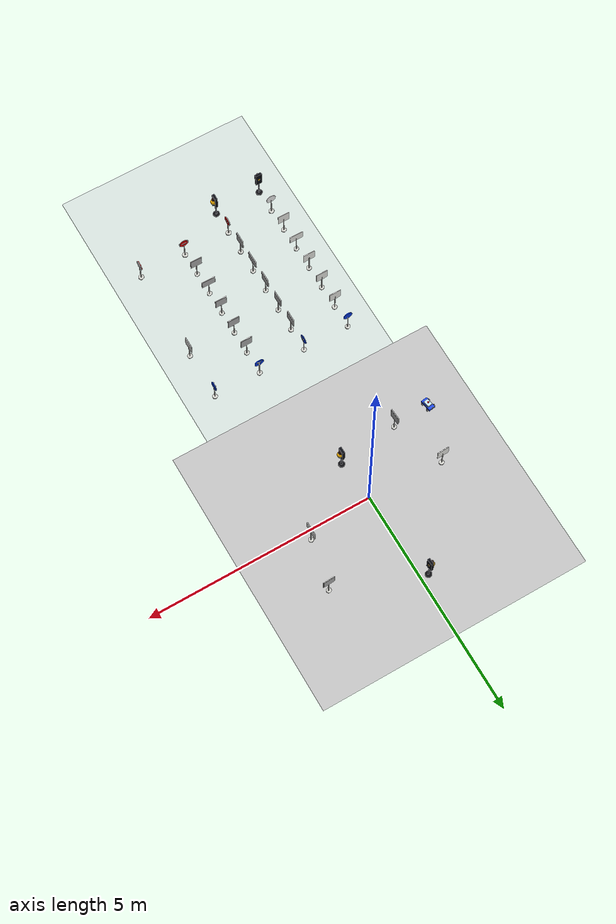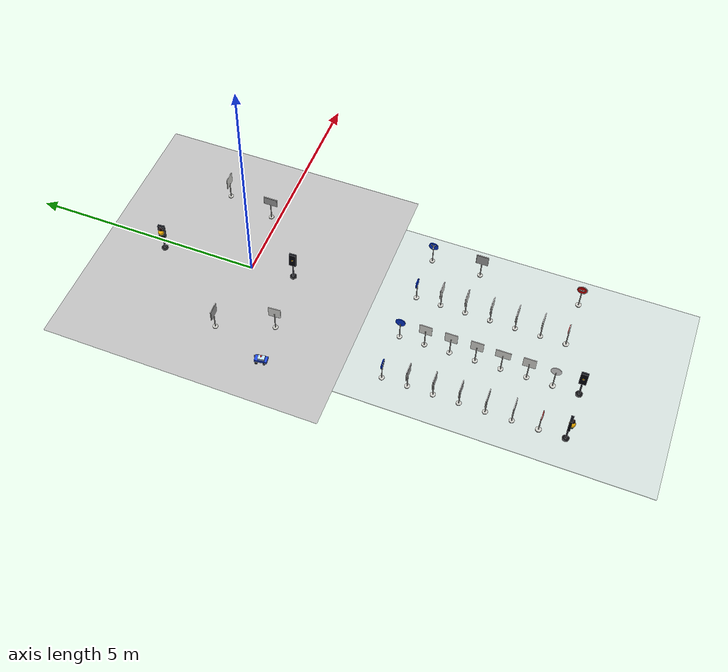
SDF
<sdf version="1.7">
 <world name="autonomous_map_3d_world">
  <plugin name="gazebo_ros_state" filename="libgazebo_ros_state.so"><update_rate>50.0</update_rate></plugin>
  <scene>
   <ambient>0.82 0.82 0.82 1</ambient>
   <background>0.86 0.91 0.98 1</background>
   <shadows>0</shadows>
  </scene>
  <light name="sun" type="directional">
   <pose>-0 0 10 0 -0 -3.14159</pose>
   <diffuse>0.8 0.8 0.8 1</diffuse>
   <specular>0.2 0.2 0.2 1</specular>
   <attenuation>
    <range>1000</range>
    <constant>0.9</constant>
    <linear>0.01</linear>
    <quadratic>0.001</quadratic>
   </attenuation>
   <direction>-0.5 0.1 -0.9</direction>
   <spot><inner_angle>0</inner_angle><outer_angle>0</outer_angle><falloff>0</falloff></spot>
  </light>
  <light name="key_light" type="directional">
   <cast_shadows>0</cast_shadows>
   <pose>-0 0 6 0 -0 -3.14159</pose>
   <diffuse>0.92 0.92 0.9 1</diffuse>
   <specular>0.15 0.15 0.15 1</specular>
   <direction>-0.3 0.35 -1</direction>
   <attenuation><range>10</range></attenuation>
   <spot><inner_angle>0</inner_angle><outer_angle>0</outer_angle><falloff>0</falloff></spot>
  </light>
  <light name="fill_light" type="directional">
   <cast_shadows>0</cast_shadows>
   <pose>-0 0 6 0 -0 -3.14159</pose>
   <diffuse>0.42 0.46 0.52 1</diffuse>
   <specular>0.05 0.05 0.05 1</specular>
   <direction>0.3 -0.2 -1</direction>
   <attenuation><range>10</range></attenuation>
   <spot><inner_angle>0</inner_angle><outer_angle>0</outer_angle><falloff>0</falloff></spot>
  </light>
  <model name="autonomous_map_3d_mirror_x">
   <static>1</static>
   <link name="map_link">
    <visual name="textured_map_visual">
     <geometry>
      <mesh>
       <uri>file:///home/quocbao/my_robot_vision_full_project/my_robot_vision/models/autonomous_map_3d_mirror_x/meshes/autonomous_map_3d_mirror_x.dae</uri>
      </mesh>
     </geometry>
    </visual>
    <collision name="floor_collision">
     <pose>0 0 -0.01 0 -0 0</pose>
     <geometry><box><size>6 6 0.02</size></box></geometry>
    </collision>
   </link>
   <pose>0 0.3 0 0 -0 -3.14159</pose>
  </model>
  <model name="sign_palette_floor_outside_map">
   <static>1</static>
   <link name="palette_floor_link">
    <visual name="palette_floor_visual">
     <geometry><box><size>4.4 6.41 0.02</size></box></geometry>
     <material><ambient>0.78 0.8 0.82 0.55</ambient><diffuse>0.78 0.8 0.82 0.55</diffuse></material>
    </visual>
    <collision name="palette_floor_collision">
     <geometry><box><size>4.4 6.41 0.02</size></box></geometry>
    </collision>
   </link>
   <pose>0.000801 -5.87455 -0.02 0 -0 0</pose>
  </model>
  <model name="palette_arrow_00_yaw_000">
   <static>1</static>
   <link name="arrow_sign_link">
    <visual name="base_visual">
     <pose>0 0 0.01 0 -0 0</pose>
     <geometry><cylinder><radius>0.055</radius><length>0.02</length></cylinder></geometry>
     <material><ambient>0.72 0.72 0.7 1</ambient><diffuse>0.78 0.78 0.76 1</diffuse></material>
    </visual>
    <visual name="pole_visual">
     <pose>0 0 0.23 0 -0 0</pose>
     <geometry><cylinder><radius>0.01</radius><length>0.44</length></cylinder></geometry>
     <material><ambient>0.72 0.72 0.7 1</ambient><diffuse>0.82 0.82 0.8 1</diffuse></material>
    </visual>
    <visual name="blue_plate_visual">
     <pose>0 -0.004 0.5 1.5708 -0 0</pose>
     <geometry><cylinder><radius>0.102</radius><length>0.014</length></cylinder></geometry>
     <material><ambient>0.02 0.18 0.68 1</ambient><diffuse>0.03 0.24 0.92 1</diffuse></material>
    </visual>
    <visual name="arrow_stem_visual">
     <pose>0 -0.018 0.475 0 -0 0</pose>
     <geometry><box><size>0.03 0.006 0.105</size></box></geometry>
     <material><ambient>1 1 1 1</ambient><diffuse>1 1 1 1</diffuse></material>
    </visual>
    <visual name="arrow_head_left_visual">
     <pose>-0.028 -0.02 0.545 0 -0.75 0</pose>
     <geometry><box><size>0.02 0.006 0.075</size></box></geometry>
     <material><ambient>1 1 1 1</ambient><diffuse>1 1 1 1</diffuse></material>
    </visual>
    <visual name="arrow_head_right_visual">
     <pose>0.028 -0.02 0.545 0 0.75 0</pose>
     <geometry><box><size>0.02 0.006 0.075</size></box></geometry>
     <material><ambient>1 1 1 1</ambient><diffuse>1 1 1 1</diffuse></material>
    </visual>
   </link>
   <pose>-1.575 -3.5 0 0 -0 0</pose>
  </model>
  <model name="palette_arrow_01_yaw_090">
   <static>1</static>
   <link name="arrow_sign_link">
    <visual name="base_visual">
     <pose>0 0 0.01 0 -0 0</pose>
     <geometry><cylinder><radius>0.055</radius><length>0.02</length></cylinder></geometry>
     <material><ambient>0.72 0.72 0.7 1</ambient><diffuse>0.78 0.78 0.76 1</diffuse></material>
    </visual>
    <visual name="pole_visual">
     <pose>0 0 0.23 0 -0 0</pose>
     <geometry><cylinder><radius>0.01</radius><length>0.44</length></cylinder></geometry>
     <material><ambient>0.72 0.72 0.7 1</ambient><diffuse>0.82 0.82 0.8 1</diffuse></material>
    </visual>
    <visual name="blue_plate_visual">
     <pose>0 -0.004 0.5 1.5708 -0 0</pose>
     <geometry><cylinder><radius>0.102</radius><length>0.014</length></cylinder></geometry>
     <material><ambient>0.02 0.18 0.68 1</ambient><diffuse>0.03 0.24 0.92 1</diffuse></material>
    </visual>
    <visual name="arrow_stem_visual">
     <pose>0 -0.018 0.475 0 -0 0</pose>
     <geometry><box><size>0.03 0.006 0.105</size></box></geometry>
     <material><ambient>1 1 1 1</ambient><diffuse>1 1 1 1</diffuse></material>
    </visual>
    <visual name="arrow_head_left_visual">
     <pose>-0.028 -0.02 0.545 0 -0.75 0</pose>
     <geometry><box><size>0.02 0.006 0.075</size></box></geometry>
     <material><ambient>1 1 1 1</ambient><diffuse>1 1 1 1</diffuse></material>
    </visual>
    <visual name="arrow_head_right_visual">
     <pose>0.028 -0.02 0.545 0 0.75 0</pose>
     <geometry><box><size>0.02 0.006 0.075</size></box></geometry>
     <material><ambient>1 1 1 1</ambient><diffuse>1 1 1 1</diffuse></material>
    </visual>
   </link>
   <pose>-0.525 -3.5 0 0 -0 1.5708</pose>
  </model>
  <model name="palette_arrow_02_yaw_180">
   <static>1</static>
   <link name="arrow_sign_link">
    <visual name="base_visual">
     <pose>0 0 0.01 0 -0 0</pose>
     <geometry><cylinder><radius>0.055</radius><length>0.02</length></cylinder></geometry>
     <material><ambient>0.72 0.72 0.7 1</ambient><diffuse>0.78 0.78 0.76 1</diffuse></material>
    </visual>
    <visual name="pole_visual">
     <pose>0 0 0.23 0 -0 0</pose>
     <geometry><cylinder><radius>0.01</radius><length>0.44</length></cylinder></geometry>
     <material><ambient>0.72 0.72 0.7 1</ambient><diffuse>0.82 0.82 0.8 1</diffuse></material>
    </visual>
    <visual name="blue_plate_visual">
     <pose>0 -0.004 0.5 1.5708 -0 0</pose>
     <geometry><cylinder><radius>0.102</radius><length>0.014</length></cylinder></geometry>
     <material><ambient>0.02 0.18 0.68 1</ambient><diffuse>0.03 0.24 0.92 1</diffuse></material>
    </visual>
    <visual name="arrow_stem_visual">
     <pose>0 -0.018 0.475 0 -0 0</pose>
     <geometry><box><size>0.03 0.006 0.105</size></box></geometry>
     <material><ambient>1 1 1 1</ambient><diffuse>1 1 1 1</diffuse></material>
    </visual>
    <visual name="arrow_head_left_visual">
     <pose>-0.028 -0.02 0.545 0 -0.75 0</pose>
     <geometry><box><size>0.02 0.006 0.075</size></box></geometry>
     <material><ambient>1 1 1 1</ambient><diffuse>1 1 1 1</diffuse></material>
    </visual>
    <visual name="arrow_head_right_visual">
     <pose>0.028 -0.02 0.545 0 0.75 0</pose>
     <geometry><box><size>0.02 0.006 0.075</size></box></geometry>
     <material><ambient>1 1 1 1</ambient><diffuse>1 1 1 1</diffuse></material>
    </visual>
   </link>
   <pose>0.525 -3.5 0 0 -0 -3.14159</pose>
  </model>
  <model name="palette_arrow_03_yaw_270">
   <static>1</static>
   <link name="arrow_sign_link">
    <visual name="base_visual">
     <pose>0 0 0.01 0 -0 0</pose>
     <geometry><cylinder><radius>0.055</radius><length>0.02</length></cylinder></geometry>
     <material><ambient>0.72 0.72 0.7 1</ambient><diffuse>0.78 0.78 0.76 1</diffuse></material>
    </visual>
    <visual name="pole_visual">
     <pose>0 0 0.23 0 -0 0</pose>
     <geometry><cylinder><radius>0.01</radius><length>0.44</length></cylinder></geometry>
     <material><ambient>0.72 0.72 0.7 1</ambient><diffuse>0.82 0.82 0.8 1</diffuse></material>
    </visual>
    <visual name="blue_plate_visual">
     <pose>0 -0.004 0.5 1.5708 -0 0</pose>
     <geometry><cylinder><radius>0.102</radius><length>0.014</length></cylinder></geometry>
     <material><ambient>0.02 0.18 0.68 1</ambient><diffuse>0.03 0.24 0.92 1</diffuse></material>
    </visual>
    <visual name="arrow_stem_visual">
     <pose>0 -0.018 0.475 0 -0 0</pose>
     <geometry><box><size>0.03 0.006 0.105</size></box></geometry>
     <material><ambient>1 1 1 1</ambient><diffuse>1 1 1 1</diffuse></material>
    </visual>
    <visual name="arrow_head_left_visual">
     <pose>-0.028 -0.02 0.545 0 -0.75 0</pose>
     <geometry><box><size>0.02 0.006 0.075</size></box></geometry>
     <material><ambient>1 1 1 1</ambient><diffuse>1 1 1 1</diffuse></material>
    </visual>
    <visual name="arrow_head_right_visual">
     <pose>0.028 -0.02 0.545 0 0.75 0</pose>
     <geometry><box><size>0.02 0.006 0.075</size></box></geometry>
     <material><ambient>1 1 1 1</ambient><diffuse>1 1 1 1</diffuse></material>
    </visual>
   </link>
   <pose>1.575 -3.5 0 0 0 -1.5708</pose>
  </model>
  <model name="palette_go_straight_00_yaw_000">
   <static>1</static>
   <link name="sign_link">
    <visual name="base_visual">
     <pose>0 0 0.01 0 -0 0</pose>
     <geometry><cylinder><radius>0.055</radius><length>0.02</length></cylinder></geometry>
     <material><ambient>0.72 0.72 0.7 1</ambient><diffuse>0.78 0.78 0.76 1</diffuse></material>
    </visual>
    <visual name="pole_visual">
     <pose>0 0 0.245 0 -0 0</pose>
     <geometry><cylinder><radius>0.011</radius><length>0.47</length></cylinder></geometry>
     <material><ambient>0.72 0.72 0.7 1</ambient><diffuse>0.82 0.82 0.8 1</diffuse></material>
    </visual>
    <visual name="back_plate_visual">
     <pose>0 0 0.52 0 -0 0</pose>
     <geometry><box><size>0.26 0.014 0.26</size></box></geometry>
     <material><ambient>0.96 0.96 0.94 1</ambient><diffuse>0.98 0.98 0.96 1</diffuse></material>
    </visual>
    <visual name="sign_face_visual">
     <pose>0 -0.011 0.52 0 -0 0</pose>
     <geometry><box><size>0.246 0.004 0.246</size></box></geometry>
     <material>
      <script>
       <uri>model://road_sign_go_straight/materials/scripts</uri>
       <uri>model://road_sign_go_straight/materials/textures</uri>
       <name>RoadSign/GoStraight</name>
      </script>
     </material>
    </visual>
   </link>
   <pose>-1.575 -4.03 0 0 -0 0</pose>
  </model>
  <model name="palette_go_straight_01_yaw_090">
   <static>1</static>
   <link name="sign_link">
    <visual name="base_visual">
     <pose>0 0 0.01 0 -0 0</pose>
     <geometry><cylinder><radius>0.055</radius><length>0.02</length></cylinder></geometry>
     <material><ambient>0.72 0.72 0.7 1</ambient><diffuse>0.78 0.78 0.76 1</diffuse></material>
    </visual>
    <visual name="pole_visual">
     <pose>0 0 0.245 0 -0 0</pose>
     <geometry><cylinder><radius>0.011</radius><length>0.47</length></cylinder></geometry>
     <material><ambient>0.72 0.72 0.7 1</ambient><diffuse>0.82 0.82 0.8 1</diffuse></material>
    </visual>
    <visual name="back_plate_visual">
     <pose>0 0 0.52 0 -0 0</pose>
     <geometry><box><size>0.26 0.014 0.26</size></box></geometry>
     <material><ambient>0.96 0.96 0.94 1</ambient><diffuse>0.98 0.98 0.96 1</diffuse></material>
    </visual>
    <visual name="sign_face_visual">
     <pose>0 -0.011 0.52 0 -0 0</pose>
     <geometry><box><size>0.246 0.004 0.246</size></box></geometry>
     <material>
      <script>
       <uri>model://road_sign_go_straight/materials/scripts</uri>
       <uri>model://road_sign_go_straight/materials/textures</uri>
       <name>RoadSign/GoStraight</name>
      </script>
     </material>
    </visual>
   </link>
   <pose>-0.525 -4.03 0 0 -0 1.5708</pose>
  </model>
  <model name="palette_go_straight_02_yaw_180">
   <static>1</static>
   <link name="sign_link">
    <visual name="base_visual">
     <pose>0 0 0.01 0 -0 0</pose>
     <geometry><cylinder><radius>0.055</radius><length>0.02</length></cylinder></geometry>
     <material><ambient>0.72 0.72 0.7 1</ambient><diffuse>0.78 0.78 0.76 1</diffuse></material>
    </visual>
    <visual name="pole_visual">
     <pose>0 0 0.245 0 -0 0</pose>
     <geometry><cylinder><radius>0.011</radius><length>0.47</length></cylinder></geometry>
     <material><ambient>0.72 0.72 0.7 1</ambient><diffuse>0.82 0.82 0.8 1</diffuse></material>
    </visual>
    <visual name="back_plate_visual">
     <pose>0 0 0.52 0 -0 0</pose>
     <geometry><box><size>0.26 0.014 0.26</size></box></geometry>
     <material><ambient>0.96 0.96 0.94 1</ambient><diffuse>0.98 0.98 0.96 1</diffuse></material>
    </visual>
    <visual name="sign_face_visual">
     <pose>0 -0.011 0.52 0 -0 0</pose>
     <geometry><box><size>0.246 0.004 0.246</size></box></geometry>
     <material>
      <script>
       <uri>model://road_sign_go_straight/materials/scripts</uri>
       <uri>model://road_sign_go_straight/materials/textures</uri>
       <name>RoadSign/GoStraight</name>
      </script>
     </material>
    </visual>
   </link>
   <pose>0.525 -4.03 0 0 -0 -3.14159</pose>
  </model>
  <model name="palette_go_straight_03_yaw_270">
   <static>1</static>
   <link name="sign_link">
    <visual name="base_visual">
     <pose>0 0 0.01 0 -0 0</pose>
     <geometry><cylinder><radius>0.055</radius><length>0.02</length></cylinder></geometry>
     <material><ambient>0.72 0.72 0.7 1</ambient><diffuse>0.78 0.78 0.76 1</diffuse></material>
    </visual>
    <visual name="pole_visual">
     <pose>0 0 0.245 0 -0 0</pose>
     <geometry><cylinder><radius>0.011</radius><length>0.47</length></cylinder></geometry>
     <material><ambient>0.72 0.72 0.7 1</ambient><diffuse>0.82 0.82 0.8 1</diffuse></material>
    </visual>
    <visual name="back_plate_visual">
     <pose>0 0 0.52 0 -0 0</pose>
     <geometry><box><size>0.26 0.014 0.26</size></box></geometry>
     <material><ambient>0.96 0.96 0.94 1</ambient><diffuse>0.98 0.98 0.96 1</diffuse></material>
    </visual>
    <visual name="sign_face_visual">
     <pose>0 -0.011 0.52 0 -0 0</pose>
     <geometry><box><size>0.246 0.004 0.246</size></box></geometry>
     <material>
      <script>
       <uri>model://road_sign_go_straight/materials/scripts</uri>
       <uri>model://road_sign_go_straight/materials/textures</uri>
       <name>RoadSign/GoStraight</name>
      </script>
     </material>
    </visual>
   </link>
   <pose>1.68364 1.26452 0 0 0 -3.09127</pose>
  </model>
  <model name="palette_turn_left_00_yaw_000">
   <static>1</static>
   <link name="sign_link">
    <visual name="base_visual">
     <pose>0 0 0.01 0 -0 0</pose>
     <geometry><cylinder><radius>0.055</radius><length>0.02</length></cylinder></geometry>
     <material><ambient>0.72 0.72 0.7 1</ambient><diffuse>0.78 0.78 0.76 1</diffuse></material>
    </visual>
    <visual name="pole_visual">
     <pose>0 0 0.245 0 -0 0</pose>
     <geometry><cylinder><radius>0.011</radius><length>0.47</length></cylinder></geometry>
     <material><ambient>0.72 0.72 0.7 1</ambient><diffuse>0.82 0.82 0.8 1</diffuse></material>
    </visual>
    <visual name="back_plate_visual">
     <pose>0 0 0.52 0 -0 0</pose>
     <geometry><box><size>0.26 0.014 0.26</size></box></geometry>
     <material><ambient>0.96 0.96 0.94 1</ambient><diffuse>0.98 0.98 0.96 1</diffuse></material>
    </visual>
    <visual name="sign_face_visual">
     <pose>0 -0.011 0.52 0 -0 0</pose>
     <geometry><box><size>0.246 0.004 0.246</size></box></geometry>
     <material>
      <script>
       <uri>model://road_sign_turn_left/materials/scripts</uri>
       <uri>model://road_sign_turn_left/materials/textures</uri>
       <name>RoadSign/TurnLeft</name>
      </script>
     </material>
    </visual>
   </link>
   <pose>-1.575 -4.56 0 0 -0 0</pose>
  </model>
  <model name="palette_turn_left_01_yaw_090">
   <static>1</static>
   <link name="sign_link">
    <visual name="base_visual">
     <pose>0 0 0.01 0 -0 0</pose>
     <geometry><cylinder><radius>0.055</radius><length>0.02</length></cylinder></geometry>
     <material><ambient>0.72 0.72 0.7 1</ambient><diffuse>0.78 0.78 0.76 1</diffuse></material>
    </visual>
    <visual name="pole_visual">
     <pose>0 0 0.245 0 -0 0</pose>
     <geometry><cylinder><radius>0.011</radius><length>0.47</length></cylinder></geometry>
     <material><ambient>0.72 0.72 0.7 1</ambient><diffuse>0.82 0.82 0.8 1</diffuse></material>
    </visual>
    <visual name="back_plate_visual">
     <pose>0 0 0.52 0 -0 0</pose>
     <geometry><box><size>0.26 0.014 0.26</size></box></geometry>
     <material><ambient>0.96 0.96 0.94 1</ambient><diffuse>0.98 0.98 0.96 1</diffuse></material>
    </visual>
    <visual name="sign_face_visual">
     <pose>0 -0.011 0.52 0 -0 0</pose>
     <geometry><box><size>0.246 0.004 0.246</size></box></geometry>
     <material>
      <script>
       <uri>model://road_sign_turn_left/materials/scripts</uri>
       <uri>model://road_sign_turn_left/materials/textures</uri>
       <name>RoadSign/TurnLeft</name>
      </script>
     </material>
    </visual>
   </link>
   <pose>-0.525 -4.56 0 0 -0 1.5708</pose>
  </model>
  <model name="palette_turn_left_02_yaw_180">
   <static>1</static>
   <link name="sign_link">
    <visual name="base_visual">
     <pose>0 0 0.01 0 -0 0</pose>
     <geometry><cylinder><radius>0.055</radius><length>0.02</length></cylinder></geometry>
     <material><ambient>0.72 0.72 0.7 1</ambient><diffuse>0.78 0.78 0.76 1</diffuse></material>
    </visual>
    <visual name="pole_visual">
     <pose>0 0 0.245 0 -0 0</pose>
     <geometry><cylinder><radius>0.011</radius><length>0.47</length></cylinder></geometry>
     <material><ambient>0.72 0.72 0.7 1</ambient><diffuse>0.82 0.82 0.8 1</diffuse></material>
    </visual>
    <visual name="back_plate_visual">
     <pose>0 0 0.52 0 -0 0</pose>
     <geometry><box><size>0.26 0.014 0.26</size></box></geometry>
     <material><ambient>0.96 0.96 0.94 1</ambient><diffuse>0.98 0.98 0.96 1</diffuse></material>
    </visual>
    <visual name="sign_face_visual">
     <pose>0 -0.011 0.52 0 -0 0</pose>
     <geometry><box><size>0.246 0.004 0.246</size></box></geometry>
     <material>
      <script>
       <uri>model://road_sign_turn_left/materials/scripts</uri>
       <uri>model://road_sign_turn_left/materials/textures</uri>
       <name>RoadSign/TurnLeft</name>
      </script>
     </material>
    </visual>
   </link>
   <pose>0.525 -4.56 0 0 -0 -3.14159</pose>
  </model>
  <model name="palette_turn_left_03_yaw_270">
   <static>1</static>
   <link name="sign_link">
    <visual name="base_visual">
     <pose>0 0 0.01 0 -0 0</pose>
     <geometry><cylinder><radius>0.055</radius><length>0.02</length></cylinder></geometry>
     <material><ambient>0.72 0.72 0.7 1</ambient><diffuse>0.78 0.78 0.76 1</diffuse></material>
    </visual>
    <visual name="pole_visual">
     <pose>0 0 0.245 0 -0 0</pose>
     <geometry><cylinder><radius>0.011</radius><length>0.47</length></cylinder></geometry>
     <material><ambient>0.72 0.72 0.7 1</ambient><diffuse>0.82 0.82 0.8 1</diffuse></material>
    </visual>
    <visual name="back_plate_visual">
     <pose>0 0 0.52 0 -0 0</pose>
     <geometry><box><size>0.26 0.014 0.26</size></box></geometry>
     <material><ambient>0.96 0.96 0.94 1</ambient><diffuse>0.98 0.98 0.96 1</diffuse></material>
    </visual>
    <visual name="sign_face_visual">
     <pose>0 -0.011 0.52 0 -0 0</pose>
     <geometry><box><size>0.246 0.004 0.246</size></box></geometry>
     <material>
      <script>
       <uri>model://road_sign_turn_left/materials/scripts</uri>
       <uri>model://road_sign_turn_left/materials/textures</uri>
       <name>RoadSign/TurnLeft</name>
      </script>
     </material>
    </visual>
   </link>
   <pose>1.575 -4.56 0 0 0 -1.5708</pose>
  </model>
  <model name="palette_turn_right_00_yaw_000">
   <static>1</static>
   <link name="sign_link">
    <visual name="base_visual">
     <pose>0 0 0.01 0 -0 0</pose>
     <geometry><cylinder><radius>0.055</radius><length>0.02</length></cylinder></geometry>
     <material><ambient>0.72 0.72 0.7 1</ambient><diffuse>0.78 0.78 0.76 1</diffuse></material>
    </visual>
    <visual name="pole_visual">
     <pose>0 0 0.245 0 -0 0</pose>
     <geometry><cylinder><radius>0.011</radius><length>0.47</length></cylinder></geometry>
     <material><ambient>0.72 0.72 0.7 1</ambient><diffuse>0.82 0.82 0.8 1</diffuse></material>
    </visual>
    <visual name="back_plate_visual">
     <pose>0 0 0.52 0 -0 0</pose>
     <geometry><box><size>0.26 0.014 0.26</size></box></geometry>
     <material><ambient>0.96 0.96 0.94 1</ambient><diffuse>0.98 0.98 0.96 1</diffuse></material>
    </visual>
    <visual name="sign_face_visual">
     <pose>0 -0.011 0.52 0 -0 0</pose>
     <geometry><box><size>0.246 0.004 0.246</size></box></geometry>
     <material>
      <script>
       <uri>model://road_sign_turn_right/materials/scripts</uri>
       <uri>model://road_sign_turn_right/materials/textures</uri>
       <name>RoadSign/TurnRight</name>
      </script>
     </material>
    </visual>
   </link>
   <pose>-1.575 -5.09 0 0 -0 0</pose>
  </model>
  <model name="palette_turn_right_01_yaw_090">
   <static>1</static>
   <link name="sign_link">
    <visual name="base_visual">
     <pose>0 0 0.01 0 -0 0</pose>
     <geometry><cylinder><radius>0.055</radius><length>0.02</length></cylinder></geometry>
     <material><ambient>0.72 0.72 0.7 1</ambient><diffuse>0.78 0.78 0.76 1</diffuse></material>
    </visual>
    <visual name="pole_visual">
     <pose>0 0 0.245 0 -0 0</pose>
     <geometry><cylinder><radius>0.011</radius><length>0.47</length></cylinder></geometry>
     <material><ambient>0.72 0.72 0.7 1</ambient><diffuse>0.82 0.82 0.8 1</diffuse></material>
    </visual>
    <visual name="back_plate_visual">
     <pose>0 0 0.52 0 -0 0</pose>
     <geometry><box><size>0.26 0.014 0.26</size></box></geometry>
     <material><ambient>0.96 0.96 0.94 1</ambient><diffuse>0.98 0.98 0.96 1</diffuse></material>
    </visual>
    <visual name="sign_face_visual">
     <pose>0 -0.011 0.52 0 -0 0</pose>
     <geometry><box><size>0.246 0.004 0.246</size></box></geometry>
     <material>
      <script>
       <uri>model://road_sign_turn_right/materials/scripts</uri>
       <uri>model://road_sign_turn_right/materials/textures</uri>
       <name>RoadSign/TurnRight</name>
      </script>
     </material>
    </visual>
   </link>
   <pose>-0.525 -5.09 0 0 -0 1.5708</pose>
  </model>
  <model name="palette_turn_right_02_yaw_180">
   <static>1</static>
   <link name="sign_link">
    <visual name="base_visual">
     <pose>0 0 0.01 0 -0 0</pose>
     <geometry><cylinder><radius>0.055</radius><length>0.02</length></cylinder></geometry>
     <material><ambient>0.72 0.72 0.7 1</ambient><diffuse>0.78 0.78 0.76 1</diffuse></material>
    </visual>
    <visual name="pole_visual">
     <pose>0 0 0.245 0 -0 0</pose>
     <geometry><cylinder><radius>0.011</radius><length>0.47</length></cylinder></geometry>
     <material><ambient>0.72 0.72 0.7 1</ambient><diffuse>0.82 0.82 0.8 1</diffuse></material>
    </visual>
    <visual name="back_plate_visual">
     <pose>0 0 0.52 0 -0 0</pose>
     <geometry><box><size>0.26 0.014 0.26</size></box></geometry>
     <material><ambient>0.96 0.96 0.94 1</ambient><diffuse>0.98 0.98 0.96 1</diffuse></material>
    </visual>
    <visual name="sign_face_visual">
     <pose>0 -0.011 0.52 0 -0 0</pose>
     <geometry><box><size>0.246 0.004 0.246</size></box></geometry>
     <material>
      <script>
       <uri>model://road_sign_turn_right/materials/scripts</uri>
       <uri>model://road_sign_turn_right/materials/textures</uri>
       <name>RoadSign/TurnRight</name>
      </script>
     </material>
    </visual>
   </link>
   <pose>0.525 -5.09 0 0 -0 -3.14159</pose>
  </model>
  <model name="palette_turn_right_03_yaw_270">
   <static>1</static>
   <link name="sign_link">
    <visual name="base_visual">
     <pose>0 0 0.01 0 -0 0</pose>
     <geometry><cylinder><radius>0.055</radius><length>0.02</length></cylinder></geometry>
     <material><ambient>0.72 0.72 0.7 1</ambient><diffuse>0.78 0.78 0.76 1</diffuse></material>
    </visual>
    <visual name="pole_visual">
     <pose>0 0 0.245 0 -0 0</pose>
     <geometry><cylinder><radius>0.011</radius><length>0.47</length></cylinder></geometry>
     <material><ambient>0.72 0.72 0.7 1</ambient><diffuse>0.82 0.82 0.8 1</diffuse></material>
    </visual>
    <visual name="back_plate_visual">
     <pose>0 0 0.52 0 -0 0</pose>
     <geometry><box><size>0.26 0.014 0.26</size></box></geometry>
     <material><ambient>0.96 0.96 0.94 1</ambient><diffuse>0.98 0.98 0.96 1</diffuse></material>
    </visual>
    <visual name="sign_face_visual">
     <pose>0 -0.011 0.52 0 -0 0</pose>
     <geometry><box><size>0.246 0.004 0.246</size></box></geometry>
     <material>
      <script>
       <uri>model://road_sign_turn_right/materials/scripts</uri>
       <uri>model://road_sign_turn_right/materials/textures</uri>
       <name>RoadSign/TurnRight</name>
      </script>
     </material>
    </visual>
   </link>
   <pose>-1.65249 0.076234 -0 0 -0 0.033484</pose>
  </model>
  <model name="palette_parking_00_yaw_000">
   <static>1</static>
   <link name="sign_link">
    <visual name="base_visual">
     <pose>0 0 0.01 0 -0 0</pose>
     <geometry><cylinder><radius>0.055</radius><length>0.02</length></cylinder></geometry>
     <material><ambient>0.72 0.72 0.7 1</ambient><diffuse>0.78 0.78 0.76 1</diffuse></material>
    </visual>
    <visual name="pole_visual">
     <pose>0 0 0.245 0 -0 0</pose>
     <geometry><cylinder><radius>0.011</radius><length>0.47</length></cylinder></geometry>
     <material><ambient>0.72 0.72 0.7 1</ambient><diffuse>0.82 0.82 0.8 1</diffuse></material>
    </visual>
    <visual name="back_plate_visual">
     <pose>0 0 0.52 0 -0 0</pose>
     <geometry><box><size>0.31 0.014 0.21</size></box></geometry>
     <material><ambient>0.96 0.96 0.94 1</ambient><diffuse>0.98 0.98 0.96 1</diffuse></material>
    </visual>
    <visual name="sign_face_visual">
     <pose>0 -0.011 0.52 0 -0 0</pose>
     <geometry><box><size>0.294 0.004 0.196</size></box></geometry>
     <material>
      <script>
       <uri>model://road_sign_parking/materials/scripts</uri>
       <uri>model://road_sign_parking/materials/textures</uri>
       <name>RoadSign/Parking</name>
      </script>
     </material>
    </visual>
   </link>
   <pose>-1.575 -5.62 0 0 -0 0</pose>
  </model>
  <model name="palette_parking_01_yaw_090">
   <static>1</static>
   <link name="sign_link">
    <visual name="base_visual">
     <pose>0 0 0.01 0 -0 0</pose>
     <geometry><cylinder><radius>0.055</radius><length>0.02</length></cylinder></geometry>
     <material><ambient>0.72 0.72 0.7 1</ambient><diffuse>0.78 0.78 0.76 1</diffuse></material>
    </visual>
    <visual name="pole_visual">
     <pose>0 0 0.245 0 -0 0</pose>
     <geometry><cylinder><radius>0.011</radius><length>0.47</length></cylinder></geometry>
     <material><ambient>0.72 0.72 0.7 1</ambient><diffuse>0.82 0.82 0.8 1</diffuse></material>
    </visual>
    <visual name="back_plate_visual">
     <pose>0 0 0.52 0 -0 0</pose>
     <geometry><box><size>0.31 0.014 0.21</size></box></geometry>
     <material><ambient>0.96 0.96 0.94 1</ambient><diffuse>0.98 0.98 0.96 1</diffuse></material>
    </visual>
    <visual name="sign_face_visual">
     <pose>0 -0.011 0.52 0 -0 0</pose>
     <geometry><box><size>0.294 0.004 0.196</size></box></geometry>
     <material>
      <script>
       <uri>model://road_sign_parking/materials/scripts</uri>
       <uri>model://road_sign_parking/materials/textures</uri>
       <name>RoadSign/Parking</name>
      </script>
     </material>
    </visual>
   </link>
   <pose>-0.525 -5.62 0 0 -0 1.5708</pose>
  </model>
  <model name="palette_parking_02_yaw_180">
   <static>1</static>
   <link name="sign_link">
    <visual name="base_visual">
     <pose>0 0 0.01 0 -0 0</pose>
     <geometry><cylinder><radius>0.055</radius><length>0.02</length></cylinder></geometry>
     <material><ambient>0.72 0.72 0.7 1</ambient><diffuse>0.78 0.78 0.76 1</diffuse></material>
    </visual>
    <visual name="pole_visual">
     <pose>0 0 0.245 0 -0 0</pose>
     <geometry><cylinder><radius>0.011</radius><length>0.47</length></cylinder></geometry>
     <material><ambient>0.72 0.72 0.7 1</ambient><diffuse>0.82 0.82 0.8 1</diffuse></material>
    </visual>
    <visual name="back_plate_visual">
     <pose>0 0 0.52 0 -0 0</pose>
     <geometry><box><size>0.31 0.014 0.21</size></box></geometry>
     <material><ambient>0.96 0.96 0.94 1</ambient><diffuse>0.98 0.98 0.96 1</diffuse></material>
    </visual>
    <visual name="sign_face_visual">
     <pose>0 -0.011 0.52 0 -0 0</pose>
     <geometry><box><size>0.294 0.004 0.196</size></box></geometry>
     <material>
      <script>
       <uri>model://road_sign_parking/materials/scripts</uri>
       <uri>model://road_sign_parking/materials/textures</uri>
       <name>RoadSign/Parking</name>
      </script>
     </material>
    </visual>
   </link>
   <pose>0.525 -5.62 0 0 -0 -3.14159</pose>
  </model>
  <model name="palette_parking_03_yaw_270">
   <static>1</static>
   <link name="sign_link">
    <visual name="base_visual">
     <pose>0 0 0.01 0 -0 0</pose>
     <geometry><cylinder><radius>0.055</radius><length>0.02</length></cylinder></geometry>
     <material><ambient>0.72 0.72 0.7 1</ambient><diffuse>0.78 0.78 0.76 1</diffuse></material>
    </visual>
    <visual name="pole_visual">
     <pose>0 0 0.245 0 -0 0</pose>
     <geometry><cylinder><radius>0.011</radius><length>0.47</length></cylinder></geometry>
     <material><ambient>0.72 0.72 0.7 1</ambient><diffuse>0.82 0.82 0.8 1</diffuse></material>
    </visual>
    <visual name="back_plate_visual">
     <pose>0 0 0.52 0 -0 0</pose>
     <geometry><box><size>0.31 0.014 0.21</size></box></geometry>
     <material><ambient>0.96 0.96 0.94 1</ambient><diffuse>0.98 0.98 0.96 1</diffuse></material>
    </visual>
    <visual name="sign_face_visual">
     <pose>0 -0.011 0.52 0 -0 0</pose>
     <geometry><box><size>0.294 0.004 0.196</size></box></geometry>
     <material>
      <script>
       <uri>model://road_sign_parking/materials/scripts</uri>
       <uri>model://road_sign_parking/materials/textures</uri>
       <name>RoadSign/Parking</name>
      </script>
     </material>
    </visual>
   </link>
   <pose>1.45031 0.181193 0 0 0 -1.5708</pose>
  </model>
  <model name="palette_speed_limit_00_yaw_000">
   <static>1</static>
   <link name="sign_link">
    <visual name="base_visual">
     <pose>0 0 0.01 0 -0 0</pose>
     <geometry><cylinder><radius>0.055</radius><length>0.02</length></cylinder></geometry>
     <material><ambient>0.72 0.72 0.7 1</ambient><diffuse>0.78 0.78 0.76 1</diffuse></material>
    </visual>
    <visual name="pole_visual">
     <pose>0 0 0.245 0 -0 0</pose>
     <geometry><cylinder><radius>0.011</radius><length>0.47</length></cylinder></geometry>
     <material><ambient>0.72 0.72 0.7 1</ambient><diffuse>0.82 0.82 0.8 1</diffuse></material>
    </visual>
    <visual name="back_plate_visual">
     <pose>0 0 0.52 0 -0 0</pose>
     <geometry><box><size>0.26 0.014 0.26</size></box></geometry>
     <material><ambient>0.96 0.96 0.94 1</ambient><diffuse>0.98 0.98 0.96 1</diffuse></material>
    </visual>
    <visual name="sign_face_visual">
     <pose>0 -0.011 0.52 0 -0 0</pose>
     <geometry><box><size>0.246 0.004 0.246</size></box></geometry>
     <material>
      <script>
       <uri>model://road_sign_speed_limit/materials/scripts</uri>
       <uri>model://road_sign_speed_limit/materials/textures</uri>
       <name>RoadSign/SpeedLimit</name>
      </script>
     </material>
    </visual>
   </link>
   <pose>-1.575 -6.15 0 0 -0 0</pose>
  </model>
  <model name="palette_speed_limit_01_yaw_090">
   <static>1</static>
   <link name="sign_link">
    <visual name="base_visual">
     <pose>0 0 0.01 0 -0 0</pose>
     <geometry><cylinder><radius>0.055</radius><length>0.02</length></cylinder></geometry>
     <material><ambient>0.72 0.72 0.7 1</ambient><diffuse>0.78 0.78 0.76 1</diffuse></material>
    </visual>
    <visual name="pole_visual">
     <pose>0 0 0.245 0 -0 0</pose>
     <geometry><cylinder><radius>0.011</radius><length>0.47</length></cylinder></geometry>
     <material><ambient>0.72 0.72 0.7 1</ambient><diffuse>0.82 0.82 0.8 1</diffuse></material>
    </visual>
    <visual name="back_plate_visual">
     <pose>0 0 0.52 0 -0 0</pose>
     <geometry><box><size>0.26 0.014 0.26</size></box></geometry>
     <material><ambient>0.96 0.96 0.94 1</ambient><diffuse>0.98 0.98 0.96 1</diffuse></material>
    </visual>
    <visual name="sign_face_visual">
     <pose>0 -0.011 0.52 0 -0 0</pose>
     <geometry><box><size>0.246 0.004 0.246</size></box></geometry>
     <material>
      <script>
       <uri>model://road_sign_speed_limit/materials/scripts</uri>
       <uri>model://road_sign_speed_limit/materials/textures</uri>
       <name>RoadSign/SpeedLimit</name>
      </script>
     </material>
    </visual>
   </link>
   <pose>-0.525 -6.15 0 0 -0 1.5708</pose>
  </model>
  <model name="palette_speed_limit_02_yaw_180">
   <static>1</static>
   <link name="sign_link">
    <visual name="base_visual">
     <pose>0 0 0.01 0 -0 0</pose>
     <geometry><cylinder><radius>0.055</radius><length>0.02</length></cylinder></geometry>
     <material><ambient>0.72 0.72 0.7 1</ambient><diffuse>0.78 0.78 0.76 1</diffuse></material>
    </visual>
    <visual name="pole_visual">
     <pose>0 0 0.245 0 -0 0</pose>
     <geometry><cylinder><radius>0.011</radius><length>0.47</length></cylinder></geometry>
     <material><ambient>0.72 0.72 0.7 1</ambient><diffuse>0.82 0.82 0.8 1</diffuse></material>
    </visual>
    <visual name="back_plate_visual">
     <pose>0 0 0.52 0 -0 0</pose>
     <geometry><box><size>0.26 0.014 0.26</size></box></geometry>
     <material><ambient>0.96 0.96 0.94 1</ambient><diffuse>0.98 0.98 0.96 1</diffuse></material>
    </visual>
    <visual name="sign_face_visual">
     <pose>0 -0.011 0.52 0 -0 0</pose>
     <geometry><box><size>0.246 0.004 0.246</size></box></geometry>
     <material>
      <script>
       <uri>model://road_sign_speed_limit/materials/scripts</uri>
       <uri>model://road_sign_speed_limit/materials/textures</uri>
       <name>RoadSign/SpeedLimit</name>
      </script>
     </material>
    </visual>
   </link>
   <pose>0.525 -6.15 0 0 -0 -3.14159</pose>
  </model>
  <model name="palette_speed_limit_03_yaw_270">
   <static>1</static>
   <link name="sign_link">
    <visual name="base_visual">
     <pose>0 0 0.01 0 -0 0</pose>
     <geometry><cylinder><radius>0.055</radius><length>0.02</length></cylinder></geometry>
     <material><ambient>0.72 0.72 0.7 1</ambient><diffuse>0.78 0.78 0.76 1</diffuse></material>
    </visual>
    <visual name="pole_visual">
     <pose>0 0 0.245 0 -0 0</pose>
     <geometry><cylinder><radius>0.011</radius><length>0.47</length></cylinder></geometry>
     <material><ambient>0.72 0.72 0.7 1</ambient><diffuse>0.82 0.82 0.8 1</diffuse></material>
    </visual>
    <visual name="back_plate_visual">
     <pose>0 0 0.52 0 -0 0</pose>
     <geometry><box><size>0.26 0.014 0.26</size></box></geometry>
     <material><ambient>0.96 0.96 0.94 1</ambient><diffuse>0.98 0.98 0.96 1</diffuse></material>
    </visual>
    <visual name="sign_face_visual">
     <pose>0 -0.011 0.52 0 -0 0</pose>
     <geometry><box><size>0.246 0.004 0.246</size></box></geometry>
     <material>
      <script>
       <uri>model://road_sign_speed_limit/materials/scripts</uri>
       <uri>model://road_sign_speed_limit/materials/textures</uri>
       <name>RoadSign/SpeedLimit</name>
      </script>
     </material>
    </visual>
   </link>
   <pose>-1.22981 -1.07421 -0 0 -0 1.63357</pose>
  </model>
  <model name="palette_stop_00_yaw_000">
   <static>1</static>
   <link name="stop_sign_link">
    <visual name="base_visual">
     <pose>0 0 0.01 0 -0 0</pose>
     <geometry><cylinder><radius>0.06</radius><length>0.02</length></cylinder></geometry>
     <material><ambient>0.72 0.72 0.7 1</ambient><diffuse>0.78 0.78 0.76 1</diffuse></material>
    </visual>
    <visual name="pole_visual">
     <pose>0 0 0.245 0 -0 0</pose>
     <geometry><cylinder><radius>0.011</radius><length>0.47</length></cylinder></geometry>
     <material><ambient>0.72 0.72 0.7 1</ambient><diffuse>0.82 0.82 0.8 1</diffuse></material>
    </visual>
    <visual name="white_back_plate_visual">
     <pose>0 -0.002 0.52 1.5708 -0 0</pose>
     <geometry><cylinder><radius>0.108</radius><length>0.012</length></cylinder></geometry>
     <material><ambient>1 1 1 1</ambient><diffuse>1 1 1 1</diffuse></material>
    </visual>
    <visual name="red_plate_visual">
     <pose>0 -0.01 0.52 1.5708 -0 0</pose>
     <geometry><cylinder><radius>0.094</radius><length>0.014</length></cylinder></geometry>
     <material><ambient>0.72 0.02 0.02 1</ambient><diffuse>0.95 0.04 0.04 1</diffuse></material>
    </visual>
    <visual name="stop_bar_visual">
     <pose>0 -0.02 0.52 0 -0 0</pose>
     <geometry><box><size>0.11 0.006 0.028</size></box></geometry>
     <material><ambient>1 1 1 1</ambient><diffuse>1 1 1 1</diffuse></material>
    </visual>
   </link>
   <pose>-1.575 -6.68 0 0 -0 0</pose>
  </model>
  <model name="palette_stop_01_yaw_090">
   <static>1</static>
   <link name="stop_sign_link">
    <visual name="base_visual">
     <pose>0 0 0.01 0 -0 0</pose>
     <geometry><cylinder><radius>0.06</radius><length>0.02</length></cylinder></geometry>
     <material><ambient>0.72 0.72 0.7 1</ambient><diffuse>0.78 0.78 0.76 1</diffuse></material>
    </visual>
    <visual name="pole_visual">
     <pose>0 0 0.245 0 -0 0</pose>
     <geometry><cylinder><radius>0.011</radius><length>0.47</length></cylinder></geometry>
     <material><ambient>0.72 0.72 0.7 1</ambient><diffuse>0.82 0.82 0.8 1</diffuse></material>
    </visual>
    <visual name="white_back_plate_visual">
     <pose>0 -0.002 0.52 1.5708 -0 0</pose>
     <geometry><cylinder><radius>0.108</radius><length>0.012</length></cylinder></geometry>
     <material><ambient>1 1 1 1</ambient><diffuse>1 1 1 1</diffuse></material>
    </visual>
    <visual name="red_plate_visual">
     <pose>0 -0.01 0.52 1.5708 -0 0</pose>
     <geometry><cylinder><radius>0.094</radius><length>0.014</length></cylinder></geometry>
     <material><ambient>0.72 0.02 0.02 1</ambient><diffuse>0.95 0.04 0.04 1</diffuse></material>
    </visual>
    <visual name="stop_bar_visual">
     <pose>0 -0.02 0.52 0 -0 0</pose>
     <geometry><box><size>0.11 0.006 0.028</size></box></geometry>
     <material><ambient>1 1 1 1</ambient><diffuse>1 1 1 1</diffuse></material>
    </visual>
   </link>
   <pose>-0.525 -6.68 0 0 -0 1.5708</pose>
  </model>
  <model name="palette_stop_02_yaw_180">
   <static>1</static>
   <link name="stop_sign_link">
    <visual name="base_visual">
     <pose>0 0 0.01 0 -0 0</pose>
     <geometry><cylinder><radius>0.06</radius><length>0.02</length></cylinder></geometry>
     <material><ambient>0.72 0.72 0.7 1</ambient><diffuse>0.78 0.78 0.76 1</diffuse></material>
    </visual>
    <visual name="pole_visual">
     <pose>0 0 0.245 0 -0 0</pose>
     <geometry><cylinder><radius>0.011</radius><length>0.47</length></cylinder></geometry>
     <material><ambient>0.72 0.72 0.7 1</ambient><diffuse>0.82 0.82 0.8 1</diffuse></material>
    </visual>
    <visual name="white_back_plate_visual">
     <pose>0 -0.002 0.52 1.5708 -0 0</pose>
     <geometry><cylinder><radius>0.108</radius><length>0.012</length></cylinder></geometry>
     <material><ambient>1 1 1 1</ambient><diffuse>1 1 1 1</diffuse></material>
    </visual>
    <visual name="red_plate_visual">
     <pose>0 -0.01 0.52 1.5708 -0 0</pose>
     <geometry><cylinder><radius>0.094</radius><length>0.014</length></cylinder></geometry>
     <material><ambient>0.72 0.02 0.02 1</ambient><diffuse>0.95 0.04 0.04 1</diffuse></material>
    </visual>
    <visual name="stop_bar_visual">
     <pose>0 -0.02 0.52 0 -0 0</pose>
     <geometry><box><size>0.11 0.006 0.028</size></box></geometry>
     <material><ambient>1 1 1 1</ambient><diffuse>1 1 1 1</diffuse></material>
    </visual>
   </link>
   <pose>0.525 -6.68 0 0 -0 -3.14159</pose>
  </model>
  <model name="palette_stop_03_yaw_270">
   <static>1</static>
   <link name="stop_sign_link">
    <visual name="base_visual">
     <pose>0 0 0.01 0 -0 0</pose>
     <geometry><cylinder><radius>0.06</radius><length>0.02</length></cylinder></geometry>
     <material><ambient>0.72 0.72 0.7 1</ambient><diffuse>0.78 0.78 0.76 1</diffuse></material>
    </visual>
    <visual name="pole_visual">
     <pose>0 0 0.245 0 -0 0</pose>
     <geometry><cylinder><radius>0.011</radius><length>0.47</length></cylinder></geometry>
     <material><ambient>0.72 0.72 0.7 1</ambient><diffuse>0.82 0.82 0.8 1</diffuse></material>
    </visual>
    <visual name="white_back_plate_visual">
     <pose>0 -0.002 0.52 1.5708 -0 0</pose>
     <geometry><cylinder><radius>0.108</radius><length>0.012</length></cylinder></geometry>
     <material><ambient>1 1 1 1</ambient><diffuse>1 1 1 1</diffuse></material>
    </visual>
    <visual name="red_plate_visual">
     <pose>0 -0.01 0.52 1.5708 -0 0</pose>
     <geometry><cylinder><radius>0.094</radius><length>0.014</length></cylinder></geometry>
     <material><ambient>0.72 0.02 0.02 1</ambient><diffuse>0.95 0.04 0.04 1</diffuse></material>
    </visual>
    <visual name="stop_bar_visual">
     <pose>0 -0.02 0.52 0 -0 0</pose>
     <geometry><box><size>0.11 0.006 0.028</size></box></geometry>
     <material><ambient>1 1 1 1</ambient><diffuse>1 1 1 1</diffuse></material>
    </visual>
   </link>
   <pose>1.575 -6.68 0 0 0 -1.5708</pose>
  </model>
  <model name="palette_traffic_light_00_yaw_000">
   <static>1</static>
   <link name="traffic_light_link">
    <visual name="base_visual">
     <pose>0 0 0.015 0 -0 0</pose>
     <geometry><cylinder><radius>0.07</radius><length>0.03</length></cylinder></geometry>
     <material><ambient>0.03 0.03 0.04 1</ambient><diffuse>0.04 0.04 0.05 1</diffuse></material>
    </visual>
    <visual name="pole_visual">
     <pose>0 0 0.25 0 -0 0</pose>
     <geometry><cylinder><radius>0.016</radius><length>0.47</length></cylinder></geometry>
     <material><ambient>0.08 0.08 0.1 1</ambient><diffuse>0.1 0.1 0.13 1</diffuse></material>
    </visual>
    <visual name="housing_visual">
     <pose>0 -0.006 0.565 0 -0 0</pose>
     <geometry><box><size>0.145 0.055 0.34</size></box></geometry>
     <material><ambient>0.02 0.025 0.04 1</ambient><diffuse>0.03 0.035 0.06 1</diffuse></material>
    </visual>
    <visual name="red_lens_visual">
     <pose>0 -0.038 0.66 0 -0 0</pose>
     <geometry><sphere><radius>0.043</radius></sphere></geometry>
     <material>
      <ambient>0.035 0.002 0.002 1</ambient>
      <diffuse>0.06 0.004 0.004 1</diffuse>
      <emissive>0 0 0 1</emissive>
     </material>
    </visual>
    <visual name="yellow_lens_visual">
     <pose>0 -0.038 0.565 0 -0 0</pose>
     <geometry><sphere><radius>0.043</radius></sphere></geometry>
     <material>
      <ambient>0.035 0.025 0.002 1</ambient>
      <diffuse>0.06 0.045 0.004 1</diffuse>
      <emissive>0 0 0 1</emissive>
     </material>
    </visual>
    <visual name="green_lens_visual">
     <pose>0 -0.038 0.47 0 -0 0</pose>
     <geometry><sphere><radius>0.043</radius></sphere></geometry>
     <material>
      <ambient>0.002 0.04 0.004 1</ambient>
      <diffuse>0.004 0.078 0.01 1</diffuse>
      <emissive>0 0 0 1</emissive>
     </material>
    </visual>
   </link>
   <pose>-1.575 -7.21 0 0 -0 0</pose>
  </model>
  <model name="palette_traffic_light_01_yaw_090">
   <static>1</static>
   <link name="traffic_light_link">
    <visual name="base_visual">
     <pose>0 0 0.015 0 -0 0</pose>
     <geometry><cylinder><radius>0.07</radius><length>0.03</length></cylinder></geometry>
     <material><ambient>0.03 0.03 0.04 1</ambient><diffuse>0.04 0.04 0.05 1</diffuse></material>
    </visual>
    <visual name="pole_visual">
     <pose>0 0 0.25 0 -0 0</pose>
     <geometry><cylinder><radius>0.016</radius><length>0.47</length></cylinder></geometry>
     <material><ambient>0.08 0.08 0.1 1</ambient><diffuse>0.1 0.1 0.13 1</diffuse></material>
    </visual>
    <visual name="housing_visual">
     <pose>0 -0.006 0.565 0 -0 0</pose>
     <geometry><box><size>0.145 0.055 0.34</size></box></geometry>
     <material><ambient>0.02 0.025 0.04 1</ambient><diffuse>0.03 0.035 0.06 1</diffuse></material>
    </visual>
    <visual name="red_lens_visual">
     <pose>0 -0.038 0.66 0 -0 0</pose>
     <geometry><sphere><radius>0.043</radius></sphere></geometry>
     <material>
      <ambient>0.035 0.002 0.002 1</ambient>
      <diffuse>0.06 0.004 0.004 1</diffuse>
      <emissive>0 0 0 1</emissive>
     </material>
    </visual>
    <visual name="yellow_lens_visual">
     <pose>0 -0.038 0.565 0 -0 0</pose>
     <geometry><sphere><radius>0.043</radius></sphere></geometry>
     <material>
      <ambient>0.035 0.025 0.002 1</ambient>
      <diffuse>0.06 0.045 0.004 1</diffuse>
      <emissive>0 0 0 1</emissive>
     </material>
    </visual>
    <visual name="green_lens_visual">
     <pose>0 -0.038 0.47 0 -0 0</pose>
     <geometry><sphere><radius>0.043</radius></sphere></geometry>
     <material>
      <ambient>0.002 0.04 0.004 1</ambient>
      <diffuse>0.004 0.078 0.01 1</diffuse>
      <emissive>0 0 0 1</emissive>
     </material>
    </visual>
   </link>
   <pose>-0.525 -7.21 0 0 -0 1.5708</pose>
  </model>
  <model name="palette_traffic_light_02_yaw_180">
   <static>1</static>
   <link name="traffic_light_link">
    <visual name="base_visual">
     <pose>0 0 0.015 0 -0 0</pose>
     <geometry><cylinder><radius>0.07</radius><length>0.03</length></cylinder></geometry>
     <material><ambient>0.03 0.03 0.04 1</ambient><diffuse>0.04 0.04 0.05 1</diffuse></material>
    </visual>
    <visual name="pole_visual">
     <pose>0 0 0.25 0 -0 0</pose>
     <geometry><cylinder><radius>0.016</radius><length>0.47</length></cylinder></geometry>
     <material><ambient>0.08 0.08 0.1 1</ambient><diffuse>0.1 0.1 0.13 1</diffuse></material>
    </visual>
    <visual name="housing_visual">
     <pose>0 -0.006 0.565 0 -0 0</pose>
     <geometry><box><size>0.145 0.055 0.34</size></box></geometry>
     <material><ambient>0.02 0.025 0.04 1</ambient><diffuse>0.03 0.035 0.06 1</diffuse></material>
    </visual>
    <visual name="red_lens_visual">
     <pose>0 -0.038 0.66 0 -0 0</pose>
     <geometry><sphere><radius>0.043</radius></sphere></geometry>
     <material>
      <ambient>0.035 0.002 0.002 1</ambient>
      <diffuse>0.06 0.004 0.004 1</diffuse>
      <emissive>0 0 0 1</emissive>
     </material>
    </visual>
    <visual name="yellow_lens_visual">
     <pose>0 -0.038 0.565 0 -0 0</pose>
     <geometry><sphere><radius>0.043</radius></sphere></geometry>
     <material>
      <ambient>0.035 0.025 0.002 1</ambient>
      <diffuse>0.06 0.045 0.004 1</diffuse>
      <emissive>0 0 0 1</emissive>
     </material>
    </visual>
    <visual name="green_lens_visual">
     <pose>0 -0.038 0.47 0 -0 0</pose>
     <geometry><sphere><radius>0.043</radius></sphere></geometry>
     <material>
      <ambient>0.002 0.04 0.004 1</ambient>
      <diffuse>0.004 0.078 0.01 1</diffuse>
      <emissive>0 0 0 1</emissive>
     </material>
    </visual>
   </link>
   <pose>0.106403 -0.906696 -0 0 -0 1.5941</pose>
  </model>
  <model name="palette_traffic_light_03_yaw_270">
   <static>1</static>
   <link name="traffic_light_link">
    <visual name="base_visual">
     <pose>0 0 0.015 0 -0 0</pose>
     <geometry><cylinder><radius>0.07</radius><length>0.03</length></cylinder></geometry>
     <material><ambient>0.03 0.03 0.04 1</ambient><diffuse>0.04 0.04 0.05 1</diffuse></material>
    </visual>
    <visual name="pole_visual">
     <pose>0 0 0.25 0 -0 0</pose>
     <geometry><cylinder><radius>0.016</radius><length>0.47</length></cylinder></geometry>
     <material><ambient>0.08 0.08 0.1 1</ambient><diffuse>0.1 0.1 0.13 1</diffuse></material>
    </visual>
    <visual name="housing_visual">
     <pose>0 -0.006 0.565 0 -0 0</pose>
     <geometry><box><size>0.145 0.055 0.34</size></box></geometry>
     <material><ambient>0.02 0.025 0.04 1</ambient><diffuse>0.03 0.035 0.06 1</diffuse></material>
    </visual>
    <visual name="red_lens_visual">
     <pose>0 -0.038 0.66 0 -0 0</pose>
     <geometry><sphere><radius>0.043</radius></sphere></geometry>
     <material>
      <ambient>0.035 0.002 0.002 1</ambient>
      <diffuse>0.06 0.004 0.004 1</diffuse>
      <emissive>0 0 0 1</emissive>
     </material>
    </visual>
    <visual name="yellow_lens_visual">
     <pose>0 -0.038 0.565 0 -0 0</pose>
     <geometry><sphere><radius>0.043</radius></sphere></geometry>
     <material>
      <ambient>0.035 0.025 0.002 1</ambient>
      <diffuse>0.06 0.045 0.004 1</diffuse>
      <emissive>0 0 0 1</emissive>
     </material>
    </visual>
    <visual name="green_lens_visual">
     <pose>0 -0.038 0.47 0 -0 0</pose>
     <geometry><sphere><radius>0.043</radius></sphere></geometry>
     <material>
      <ambient>0.002 0.04 0.004 1</ambient>
      <diffuse>0.004 0.078 0.01 1</diffuse>
      <emissive>0 0 0 1</emissive>
     </material>
    </visual>
   </link>
   <pose>-0.176849 1.96838 0 0 -0 -1.48449</pose>
  </model>
  <model name="palette_traffic_light_00_yaw_000_red_active_lamp">
   <static>0</static>
   <link name="lamp_link">
    <gravity>0</gravity>
    <visual name="lamp_visual">
     <geometry><sphere><radius>0.065</radius></sphere></geometry>
     <material><ambient>1 0 0 1</ambient><diffuse>1 0 0 1</diffuse><emissive>0.0313726 0 0 1</emissive></material>
    </visual>
    <kinematic>1</kinematic>
    <inertial>
     <mass>1</mass>
     <inertia><ixx>1</ixx><iyy>1</iyy><izz>1</izz><ixy>0</ixy><ixz>0</ixz><iyz>0</iyz></inertia>
    </inertial>
   </link>
   <pose>0 0 -5 0 -0 0</pose>
  </model>
  <model name="palette_traffic_light_01_yaw_090_red_active_lamp">
   <static>0</static>
   <link name="lamp_link">
    <gravity>0</gravity>
    <visual name="lamp_visual">
     <geometry><sphere><radius>0.065</radius></sphere></geometry>
     <material><ambient>1 0 0 1</ambient><diffuse>1 0 0 1</diffuse><emissive>0.0313726 0 0 1</emissive></material>
    </visual>
    <kinematic>1</kinematic>
    <inertial>
     <mass>1</mass>
     <inertia><ixx>1</ixx><iyy>1</iyy><izz>1</izz><ixy>0</ixy><ixz>0</ixz><iyz>0</iyz></inertia>
    </inertial>
   </link>
   <pose>0 0 -5 0 -0 0</pose>
  </model>
  <model name="palette_traffic_light_02_yaw_180_red_active_lamp">
   <static>0</static>
   <link name="lamp_link">
    <gravity>0</gravity>
    <visual name="lamp_visual">
     <geometry><sphere><radius>0.065</radius></sphere></geometry>
     <material><ambient>1 0 0 1</ambient><diffuse>1 0 0 1</diffuse><emissive>0.0313726 0 0 1</emissive></material>
    </visual>
    <kinematic>1</kinematic>
    <inertial>
     <mass>1</mass>
     <inertia><ixx>1</ixx><iyy>1</iyy><izz>1</izz><ixy>0</ixy><ixz>0</ixz><iyz>0</iyz></inertia>
    </inertial>
   </link>
   <pose>0 0 -5 0 -0 0</pose>
  </model>
  <model name="palette_traffic_light_03_yaw_270_red_active_lamp">
   <static>0</static>
   <link name="lamp_link">
    <gravity>0</gravity>
    <visual name="lamp_visual">
     <geometry><sphere><radius>0.065</radius></sphere></geometry>
     <material><ambient>1 0 0 1</ambient><diffuse>1 0 0 1</diffuse><emissive>0.0313726 0 0 1</emissive></material>
    </visual>
    <kinematic>1</kinematic>
    <inertial>
     <mass>1</mass>
     <inertia><ixx>1</ixx><iyy>1</iyy><izz>1</izz><ixy>0</ixy><ixz>0</ixz><iyz>0</iyz></inertia>
    </inertial>
   </link>
   <pose>0 0 -5 0 -0 0</pose>
  </model>
  <model name="palette_traffic_light_00_yaw_000_yellow_active_lamp">
   <static>0</static>
   <link name="lamp_link">
    <gravity>0</gravity>
    <visual name="lamp_visual">
     <geometry><sphere><radius>0.065</radius></sphere></geometry>
     <material>
      <ambient>1 0.72 0 1</ambient>
      <diffuse>1 0.72 0 1</diffuse>
      <emissive>0.0313726 0.0203922 0 1</emissive>
     </material>
    </visual>
    <kinematic>1</kinematic>
    <inertial>
     <mass>1</mass>
     <inertia><ixx>1</ixx><iyy>1</iyy><izz>1</izz><ixy>0</ixy><ixz>0</ixz><iyz>0</iyz></inertia>
    </inertial>
   </link>
   <pose>-1.575 -7.248 0.565 0 -0 0</pose>
  </model>
  <model name="palette_traffic_light_01_yaw_090_yellow_active_lamp">
   <static>0</static>
   <link name="lamp_link">
    <gravity>0</gravity>
    <visual name="lamp_visual">
     <geometry><sphere><radius>0.065</radius></sphere></geometry>
     <material>
      <ambient>1 0.72 0 1</ambient>
      <diffuse>1 0.72 0 1</diffuse>
      <emissive>0.0313726 0.0203922 0 1</emissive>
     </material>
    </visual>
    <kinematic>1</kinematic>
    <inertial>
     <mass>1</mass>
     <inertia><ixx>1</ixx><iyy>1</iyy><izz>1</izz><ixy>0</ixy><ixz>0</ixz><iyz>0</iyz></inertia>
    </inertial>
   </link>
   <pose>-0.487 -7.21 0.565 0 -0 1.5708</pose>
  </model>
  <model name="palette_traffic_light_02_yaw_180_yellow_active_lamp">
   <static>0</static>
   <link name="lamp_link">
    <gravity>0</gravity>
    <visual name="lamp_visual">
     <geometry><sphere><radius>0.065</radius></sphere></geometry>
     <material>
      <ambient>1 0.72 0 1</ambient>
      <diffuse>1 0.72 0 1</diffuse>
      <emissive>0.0313726 0.0203922 0 1</emissive>
     </material>
    </visual>
    <kinematic>1</kinematic>
    <inertial>
     <mass>1</mass>
     <inertia><ixx>1</ixx><iyy>1</iyy><izz>1</izz><ixy>0</ixy><ixz>0</ixz><iyz>0</iyz></inertia>
    </inertial>
   </link>
   <pose>0.144393 -0.905811 0.565 0 -0 1.5941</pose>
  </model>
  <model name="palette_traffic_light_03_yaw_270_yellow_active_lamp">
   <static>0</static>
   <link name="lamp_link">
    <gravity>0</gravity>
    <visual name="lamp_visual">
     <geometry><sphere><radius>0.065</radius></sphere></geometry>
     <material>
      <ambient>1 0.72 0 1</ambient>
      <diffuse>1 0.72 0 1</diffuse>
      <emissive>0.0313726 0.0203922 0 1</emissive>
     </material>
    </visual>
    <kinematic>1</kinematic>
    <inertial>
     <mass>1</mass>
     <inertia><ixx>1</ixx><iyy>1</iyy><izz>1</izz><ixy>0</ixy><ixz>0</ixz><iyz>0</iyz></inertia>
    </inertial>
   </link>
   <pose>-0.214708 1.9651 0.565 0 0 -1.48449</pose>
  </model>
  <model name="palette_traffic_light_00_yaw_000_green_active_lamp">
   <static>0</static>
   <link name="lamp_link">
    <gravity>0</gravity>
    <visual name="lamp_visual">
     <geometry><sphere><radius>0.065</radius></sphere></geometry>
     <material>
      <ambient>0 1 0.05 1</ambient>
      <diffuse>0 1 0.05 1</diffuse>
      <emissive>0 0.0313726 0.3 1</emissive>
     </material>
    </visual>
    <kinematic>1</kinematic>
    <inertial>
     <mass>1</mass>
     <inertia><ixx>1</ixx><iyy>1</iyy><izz>1</izz><ixy>0</ixy><ixz>0</ixz><iyz>0</iyz></inertia>
    </inertial>
   </link>
   <pose>0 0 -5 0 -0 0</pose>
  </model>
  <model name="palette_traffic_light_01_yaw_090_green_active_lamp">
   <static>0</static>
   <link name="lamp_link">
    <gravity>0</gravity>
    <visual name="lamp_visual">
     <geometry><sphere><radius>0.065</radius></sphere></geometry>
     <material>
      <ambient>0 1 0.05 1</ambient>
      <diffuse>0 1 0.05 1</diffuse>
      <emissive>0 0.0313726 0.3 1</emissive>
     </material>
    </visual>
    <kinematic>1</kinematic>
    <inertial>
     <mass>1</mass>
     <inertia><ixx>1</ixx><iyy>1</iyy><izz>1</izz><ixy>0</ixy><ixz>0</ixz><iyz>0</iyz></inertia>
    </inertial>
   </link>
   <pose>0 0 -5 0 -0 0</pose>
  </model>
  <model name="palette_traffic_light_02_yaw_180_green_active_lamp">
   <static>0</static>
   <link name="lamp_link">
    <gravity>0</gravity>
    <visual name="lamp_visual">
     <geometry><sphere><radius>0.065</radius></sphere></geometry>
     <material>
      <ambient>0 1 0.05 1</ambient>
      <diffuse>0 1 0.05 1</diffuse>
      <emissive>0 0.0313726 0.3 1</emissive>
     </material>
    </visual>
    <kinematic>1</kinematic>
    <inertial>
     <mass>1</mass>
     <inertia><ixx>1</ixx><iyy>1</iyy><izz>1</izz><ixy>0</ixy><ixz>0</ixz><iyz>0</iyz></inertia>
    </inertial>
   </link>
   <pose>0 0 -5 0 -0 0</pose>
  </model>
  <model name="palette_traffic_light_03_yaw_270_green_active_lamp">
   <static>0</static>
   <link name="lamp_link">
    <gravity>0</gravity>
    <visual name="lamp_visual">
     <geometry><sphere><radius>0.065</radius></sphere></geometry>
     <material>
      <ambient>0 1 0.05 1</ambient>
      <diffuse>0 1 0.05 1</diffuse>
      <emissive>0 0.0313726 0.3 1</emissive>
     </material>
    </visual>
    <kinematic>1</kinematic>
    <inertial>
     <mass>1</mass>
     <inertia><ixx>1</ixx><iyy>1</iyy><izz>1</izz><ixy>0</ixy><ixz>0</ixz><iyz>0</iyz></inertia>
    </inertial>
   </link>
   <pose>0 0 -5 0 -0 0</pose>
  </model>
  <model name="track_preview_car">
   <static>0</static>
   <allow_auto_disable>0</allow_auto_disable>
   <link name="body">
    <inertial>
     <mass>1</mass>
     <inertia><ixx>0.01</ixx><iyy>0.01</iyy><izz>0.01</izz><ixy>0</ixy><ixz>0</ixz><iyz>0</iyz></inertia>
    </inertial>
    <visual name="chassis_visual">
     <pose>0 0 0.065 0 -0 0</pose>
     <geometry><box><size>0.26 0.14 0.055</size></box></geometry>
     <material>
      <ambient>0.08 0.2 0.7 1</ambient>
      <diffuse>0.12 0.28 0.88 1</diffuse>
      <specular>0.1 0.1 0.1 1</specular>
     </material>
    </visual>
    <visual name="roof_visual">
     <pose>-0.005 0 0.115 0 -0 0</pose>
     <geometry><box><size>0.14 0.105 0.045</size></box></geometry>
     <material>
      <ambient>0.65 0.78 0.95 0.92</ambient>
      <diffuse>0.75 0.86 0.98 0.92</diffuse>
      <specular>0.1 0.1 0.1 1</specular>
     </material>
    </visual>
    <visual name="front_marker_visual">
     <pose>0.105 0 0.083 0 -0 0</pose>
     <geometry><box><size>0.025 0.075 0.018</size></box></geometry>
     <material>
      <ambient>1 0.85 0.2 1</ambient>
      <diffuse>1 0.88 0.25 1</diffuse>
      <specular>0.05 0.05 0.05 1</specular>
     </material>
    </visual>
    <visual name="camera_lens_visual">
     <pose>0.138 0 0.126 0 -0 0</pose>
     <geometry><box><size>0.016 0.04 0.022</size></box></geometry>
     <material>
      <ambient>0.02 0.02 0.025 1</ambient>
      <diffuse>0.04 0.04 0.05 1</diffuse>
      <specular>0.05 0.05 0.05 1</specular>
     </material>
    </visual>
    <visual name="camera_view_left_ray_visual">
     <pose>1.67 1.15 0.335 -0 0.0505 0.6109</pose>
     <geometry><box><size>0.001 0.001 0.001</size></box></geometry>
     <material>
      <ambient>0.85 1 1 0.82</ambient>
      <diffuse>0.85 1 1 0.82</diffuse>
      <emissive>0.2 0.55 0.75 1</emissive>
     </material>
    </visual>
    <visual name="camera_view_center_ray_visual">
     <pose>1.67 0 0.335 0 0.0555 0</pose>
     <geometry><box><size>0.001 0.001 0.001</size></box></geometry>
     <material>
      <ambient>0.85 1 1 0.82</ambient>
      <diffuse>0.85 1 1 0.82</diffuse>
      <emissive>0.2 0.55 0.75 1</emissive>
     </material>
    </visual>
    <visual name="camera_view_right_ray_visual">
     <pose>1.67 -1.15 0.335 0 0.0505 -0.6109</pose>
     <geometry><box><size>0.001 0.001 0.001</size></box></geometry>
     <material>
      <ambient>0.85 1 1 0.82</ambient>
      <diffuse>0.85 1 1 0.82</diffuse>
      <emissive>0.2 0.55 0.75 1</emissive>
     </material>
    </visual>
    <visual name="debug_origin_marker_visual">
     <pose>0 0 0.165 0 -0 0</pose>
     <geometry><sphere><radius>0.018</radius></sphere></geometry>
     <material>
      <ambient>1 0.02 0.02 1</ambient>
      <diffuse>1 0.04 0.04 1</diffuse>
      <specular>0.08 0.08 0.08 1</specular>
     </material>
    </visual>
    <visual name="debug_ground_origin_visual">
     <pose>0 0 -0.017 0 -0 0</pose>
     <geometry><cylinder><radius>0.018</radius><length>0.004</length></cylinder></geometry>
     <material>
      <ambient>1 0.02 0.02 1</ambient>
      <diffuse>1 0.04 0.04 1</diffuse>
      <specular>0.08 0.08 0.08 1</specular>
     </material>
    </visual>
    <visual name="debug_ground_footprint_front_visual">
     <pose>0.165 0 -0.017 0 -0 0</pose>
     <geometry><box><size>0.008 0.238 0.004</size></box></geometry>
     <material>
      <ambient>0 0.7 1 1</ambient>
      <diffuse>0.05 0.86 1 1</diffuse>
      <specular>0.02 0.02 0.02 1</specular>
     </material>
    </visual>
    <visual name="debug_ground_footprint_rear_visual">
     <pose>-0.145 0 -0.017 0 -0 0</pose>
     <geometry><box><size>0.008 0.238 0.004</size></box></geometry>
     <material>
      <ambient>0 0.7 1 1</ambient>
      <diffuse>0.05 0.86 1 1</diffuse>
      <specular>0.02 0.02 0.02 1</specular>
     </material>
    </visual>
    <visual name="debug_ground_footprint_left_visual">
     <pose>0.01 0.115 -0.017 0 -0 0</pose>
     <geometry><box><size>0.318 0.008 0.004</size></box></geometry>
     <material>
      <ambient>0 0.7 1 1</ambient>
      <diffuse>0.05 0.86 1 1</diffuse>
      <specular>0.02 0.02 0.02 1</specular>
     </material>
    </visual>
    <visual name="debug_ground_footprint_right_visual">
     <pose>0.01 -0.115 -0.017 0 -0 0</pose>
     <geometry><box><size>0.318 0.008 0.004</size></box></geometry>
     <material>
      <ambient>0 0.7 1 1</ambient>
      <diffuse>0.05 0.86 1 1</diffuse>
      <specular>0.02 0.02 0.02 1</specular>
     </material>
    </visual>
    <visual name="rear_left_dummy_wheel_visual">
     <pose>-0.08 0.085 0.032 1.5708 -0 0</pose>
     <geometry><cylinder><radius>0.028</radius><length>0.016</length></cylinder></geometry>
     <material>
      <ambient>0.03 0.03 0.03 1</ambient>
      <diffuse>0.07 0.07 0.07 1</diffuse>
      <specular>0.02 0.02 0.02 1</specular>
     </material>
    </visual>
    <visual name="rear_right_dummy_wheel_visual">
     <pose>-0.08 -0.085 0.032 1.5708 -0 0</pose>
     <geometry><cylinder><radius>0.028</radius><length>0.016</length></cylinder></geometry>
     <material>
      <ambient>0.03 0.03 0.03 1</ambient>
      <diffuse>0.07 0.07 0.07 1</diffuse>
      <specular>0.02 0.02 0.02 1</specular>
     </material>
    </visual>
    <collision name="rear_left_caster_collision">
     <pose>-0.095 0.072 0.026 0 -0 0</pose>
     <geometry><sphere><radius>0.024</radius></sphere></geometry>
     <surface><friction><ode><mu>0.05</mu><mu2>0.05</mu2></ode></friction></surface>
    </collision>
    <collision name="rear_right_caster_collision">
     <pose>-0.095 -0.072 0.026 0 -0 0</pose>
     <geometry><sphere><radius>0.024</radius></sphere></geometry>
     <surface><friction><ode><mu>0.05</mu><mu2>0.05</mu2></ode></friction></surface>
    </collision>
    <collision name="body_collision">
     <pose>0 0 0.065 0 -0 0</pose>
     <geometry><box><size>0.26 0.14 0.05</size></box></geometry>
    </collision>
    <sensor name="front_camera" type="camera">
     <pose>0.14 0 0.42 0 0.18 0</pose>
     <always_on>1</always_on>
     <update_rate>30</update_rate>
     <visualize>0</visualize>
     <camera>
      <horizontal_fov>2.45</horizontal_fov>
      <image><width>960</width><height>540</height><format>R8G8B8</format></image>
      <clip><near>0.02</near><far>6</far></clip>
     </camera>
     <plugin name="front_camera_controller" filename="libgazebo_ros_camera.so">
      <ros>
       <namespace>/track_preview_car</namespace>
       <remapping>image_raw:=image_raw</remapping>
       <remapping>camera_info:=camera_info</remapping>
      </ros>
      <camera_name>camera</camera_name>
      <frame_name>track_preview_car/front_camera</frame_name>
     </plugin>
    </sensor>
   </link>
   <link name="left_wheel">
    <pose>0.08 0.088 0.032 0 -0 0</pose>
    <inertial>
     <mass>0.08</mass>
     <inertia><ixx>5e-05</ixx><iyy>8e-05</iyy><izz>5e-05</izz><ixy>0</ixy><ixz>0</ixz><iyz>0</iyz></inertia>
    </inertial>
    <visual name="left_wheel_visual">
     <pose>0 0 0 1.5708 -0 0</pose>
     <geometry><cylinder><radius>0.03</radius><length>0.02</length></cylinder></geometry>
     <material>
      <ambient>0.03 0.03 0.03 1</ambient>
      <diffuse>0.07 0.07 0.07 1</diffuse>
      <specular>0.02 0.02 0.02 1</specular>
     </material>
    </visual>
    <collision name="left_wheel_collision">
     <pose>0 0 0 1.5708 -0 0</pose>
     <geometry><cylinder><radius>0.03</radius><length>0.02</length></cylinder></geometry>
     <surface><friction><ode><mu>1.2</mu><mu2>1.2</mu2></ode></friction></surface>
    </collision>
   </link>
   <link name="right_wheel">
    <pose>0.08 -0.088 0.032 0 -0 0</pose>
    <inertial>
     <mass>0.08</mass>
     <inertia><ixx>5e-05</ixx><iyy>8e-05</iyy><izz>5e-05</izz><ixy>0</ixy><ixz>0</ixz><iyz>0</iyz></inertia>
    </inertial>
    <visual name="right_wheel_visual">
     <pose>0 0 0 1.5708 -0 0</pose>
     <geometry><cylinder><radius>0.03</radius><length>0.02</length></cylinder></geometry>
     <material>
      <ambient>0.03 0.03 0.03 1</ambient>
      <diffuse>0.07 0.07 0.07 1</diffuse>
      <specular>0.02 0.02 0.02 1</specular>
     </material>
    </visual>
    <collision name="right_wheel_collision">
     <pose>0 0 0 1.5708 -0 0</pose>
     <geometry><cylinder><radius>0.03</radius><length>0.02</length></cylinder></geometry>
     <surface><friction><ode><mu>1.2</mu><mu2>1.2</mu2></ode></friction></surface>
    </collision>
   </link>
   <joint name="left_wheel_joint" type="revolute">
    <parent>body</parent>
    <child>left_wheel</child>
    <axis>
     <xyz>0 1 0</xyz>
     <limit><lower>-1e+16</lower><upper>1e+16</upper></limit>
     <dynamics><spring_reference>0</spring_reference><spring_stiffness>0</spring_stiffness></dynamics>
    </axis>
   </joint>
   <joint name="right_wheel_joint" type="revolute">
    <parent>body</parent>
    <child>right_wheel</child>
    <axis>
     <xyz>0 1 0</xyz>
     <limit><lower>-1e+16</lower><upper>1e+16</upper></limit>
     <dynamics><spring_reference>0</spring_reference><spring_stiffness>0</spring_stiffness></dynamics>
    </axis>
   </joint>
   <plugin name="track_preview_car_diff_drive" filename="libgazebo_ros_diff_drive.so">
    <ros>
     <namespace>/track_preview_car</namespace>
     <remapping>cmd_vel:=cmd_vel</remapping>
     <remapping>odom:=odom</remapping>
    </ros>
    <left_joint>left_wheel_joint</left_joint>
    <right_joint>right_wheel_joint</right_joint>
    <wheel_separation>0.176</wheel_separation>
    <wheel_diameter>0.06</wheel_diameter>
    <max_wheel_torque>2.0</max_wheel_torque>
    <max_wheel_acceleration>8.0</max_wheel_acceleration>
    <odometry_frame>odom</odometry_frame>
    <robot_base_frame>body</robot_base_frame>
    <publish_odom>1</publish_odom>
    <publish_odom_tf>0</publish_odom_tf>
    <publish_wheel_tf>0</publish_wheel_tf>
    <update_rate>50</update_rate>
   </plugin>
   <pose>-2.07473 -1.13292 -0.002003 3.9e-05 1.1e-05 1.71005</pose>
  </model>
  <physics name="default_physics" default="1" type="ode">
   <max_step_size>0.001</max_step_size>
   <real_time_update_rate>1000</real_time_update_rate>
   <real_time_factor>1</real_time_factor>
  </physics>
  <gravity>0 0 -9.8</gravity>
  <magnetic_field>6e-06 2.3e-05 -4.2e-05</magnetic_field>
  <atmosphere type="adiabatic"/>
  <spherical_coordinates>
   <surface_model>EARTH_WGS84</surface_model>
   <latitude_deg>0</latitude_deg>
   <longitude_deg>0</longitude_deg>
   <elevation>0</elevation>
   <heading_deg>0</heading_deg>
  </spherical_coordinates>
 </world>
</sdf>
